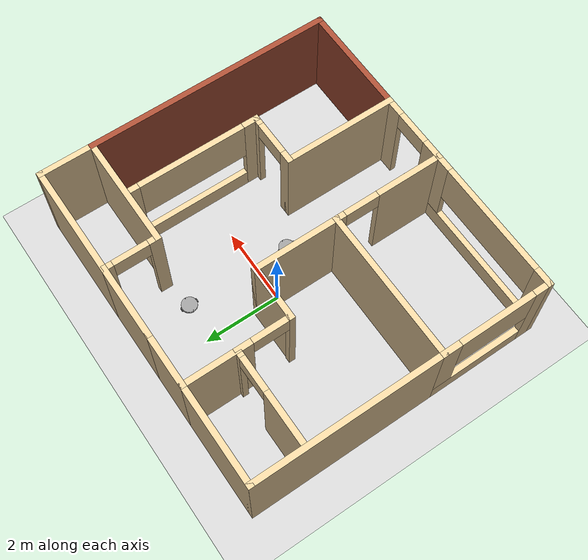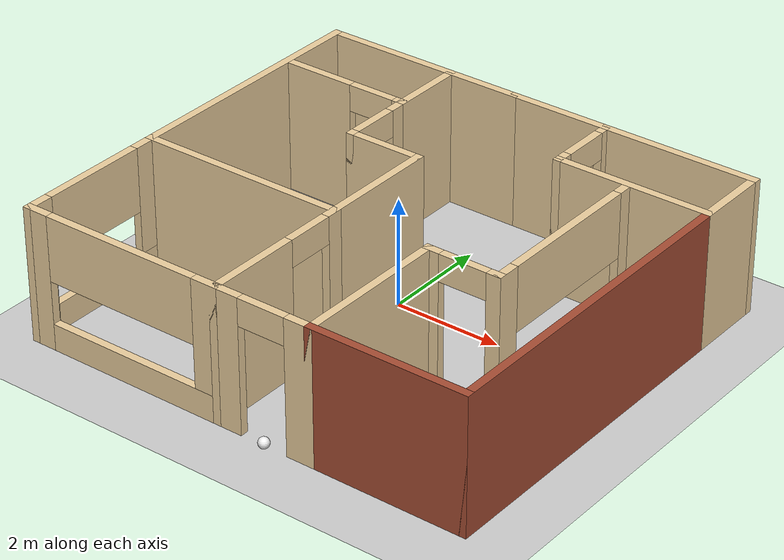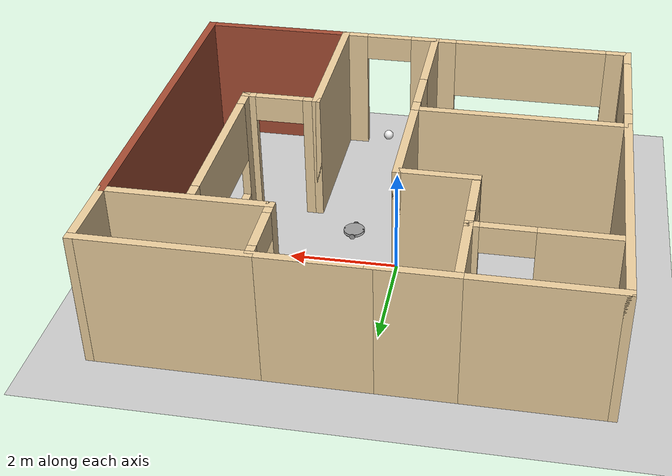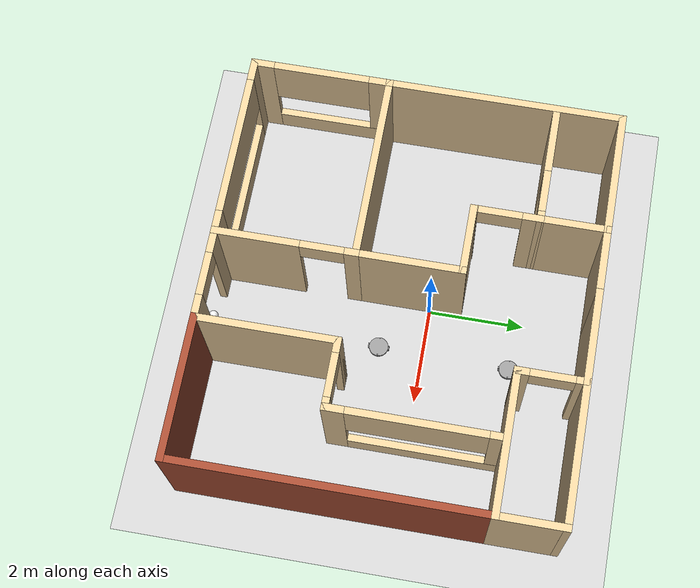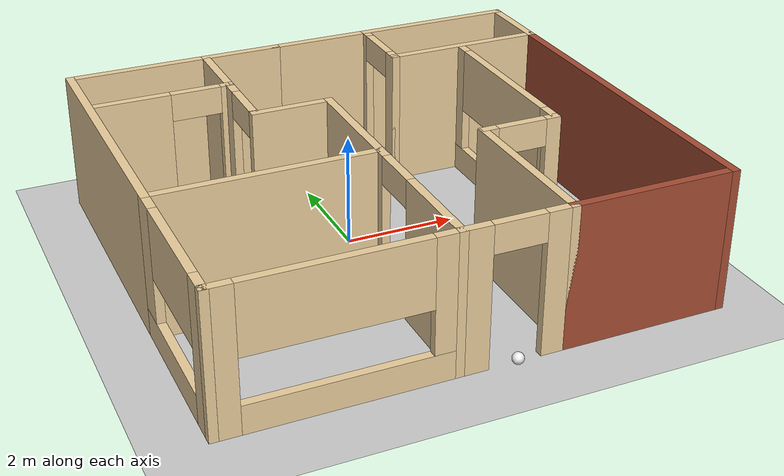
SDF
<sdf version="1.6">
 <world name="default">
  <plugin name="hello" filename="libhello.so"/>
  <light name="sun" type="directional">
   <pose>0 0 10 0 -0 0</pose>
   <diffuse>0.8 0.8 0.8 1</diffuse>
   <specular>0.2 0.2 0.2 1</specular>
   <attenuation>
    <range>1000</range>
    <constant>0.9</constant>
    <linear>0.01</linear>
    <quadratic>0.001</quadratic>
   </attenuation>
   <direction>-0.5 0.1 -0.9</direction>
  </light>
  <model name="ground_plane">
   <static>1</static>
   <link name="link">
    <collision name="collision">
     <geometry><plane><normal>0 0 1</normal><size>100 100</size></plane></geometry>
     <surface><friction><ode><mu>100</mu><mu2>50</mu2></ode></friction></surface>
    </collision>
    <visual name="visual">
     <cast_shadows>0</cast_shadows>
     <geometry><plane><normal>0 0 1</normal><size>100 100</size></plane></geometry>
     <material>
      <script><uri>file://media/materials/scripts/gazebo.material</uri><name>Gazebo/Grey</name></script>
     </material>
    </visual>
   </link>
  </model>
  <gravity>0 0 -9.8</gravity>
  <magnetic_field>6e-06 2.3e-05 -4.2e-05</magnetic_field>
  <atmosphere type="adiabatic"/>
  <physics name="default_physics" default="0" type="ode">
   <max_step_size>0.001</max_step_size>
   <real_time_factor>1</real_time_factor>
   <real_time_update_rate>1000</real_time_update_rate>
  </physics>
  <scene><ambient>0.4 0.4 0.4 1</ambient><background>0.7 0.7 0.7 1</background><shadows>1</shadows></scene>
  <spherical_coordinates>
   <surface_model>EARTH_WGS84</surface_model>
   <latitude_deg>0</latitude_deg>
   <longitude_deg>0</longitude_deg>
   <elevation>0</elevation>
   <heading_deg>0</heading_deg>
  </spherical_coordinates>
  <model name="MyHouse">
   <pose>0.33708 -0.54401 0 0 -0 0</pose>
   <link name="Wall_0">
    <pose>-2.35 -3.85 0 0 -0 0</pose>
    <visual name="Wall_0_Visual_0">
     <pose>-1.7526 0 1.25 0 -0 0</pose>
     <geometry><box><size>0.494799 0.15 2.5</size></box></geometry>
     <material>
      <script><uri>file://media/materials/scripts/gazebo.material</uri><name>Gazebo/Grey</name></script>
      <ambient>0.921569 0.807843 0.615686 1</ambient>
     </material>
     <meta><layer>0</layer></meta>
    </visual>
    <collision name="Wall_0_Collision_0">
     <geometry><box><size>0.494799 0.15 2.5</size></box></geometry>
     <pose>-1.7526 0 1.25 0 -0 0</pose>
    </collision>
    <visual name="Wall_0_Visual_1">
     <pose>0.2474 0 0.25 0 -0 0</pose>
     <geometry><box><size>3.5052 0.15 0.5</size></box></geometry>
     <material>
      <script><uri>file://media/materials/scripts/gazebo.material</uri><name>Gazebo/Grey</name></script>
      <ambient>0.921569 0.807843 0.615686 1</ambient>
     </material>
     <meta><layer>0</layer></meta>
    </visual>
    <collision name="Wall_0_Collision_1">
     <geometry><box><size>3.5052 0.15 0.5</size></box></geometry>
     <pose>0.2474 0 0.25 0 -0 0</pose>
    </collision>
    <visual name="Wall_0_Visual_2">
     <pose>1.7474 0 1.5 0 -0 0</pose>
     <geometry><box><size>0.505201 0.15 2</size></box></geometry>
     <material>
      <script><uri>file://media/materials/scripts/gazebo.material</uri><name>Gazebo/Grey</name></script>
      <ambient>0.921569 0.807843 0.615686 1</ambient>
     </material>
     <meta><layer>0</layer></meta>
    </visual>
    <collision name="Wall_0_Collision_2">
     <geometry><box><size>0.505201 0.15 2</size></box></geometry>
     <pose>1.7474 0 1.5 0 -0 0</pose>
    </collision>
    <visual name="Wall_0_Visual_3">
     <pose>-0.005201 0 1.9 0 -0 0</pose>
     <geometry><box><size>3 0.15 1.2</size></box></geometry>
     <material>
      <script><uri>file://media/materials/scripts/gazebo.material</uri><name>Gazebo/Grey</name></script>
      <ambient>0.921569 0.807843 0.615686 1</ambient>
     </material>
     <meta><layer>0</layer></meta>
    </visual>
    <collision name="Wall_0_Collision_3">
     <geometry><box><size>3 0.15 1.2</size></box></geometry>
     <pose>-0.005201 0 1.9 0 -0 0</pose>
    </collision>
   </link>
   <link name="Wall_12">
    <pose>-4.275 -2.425 0 0 -0 1.5708</pose>
    <visual name="Wall_12_Visual_0">
     <pose>-1.25263 0 1.25 0 -0 0</pose>
     <geometry><box><size>0.494741 0.15 2.5</size></box></geometry>
     <material>
      <script><uri>file://media/materials/scripts/gazebo.material</uri><name>Gazebo/Grey</name></script>
      <ambient>0.921569 0.807843 0.615686 1</ambient>
     </material>
     <meta><layer>0</layer></meta>
    </visual>
    <collision name="Wall_12_Collision_0">
     <geometry><box><size>0.494741 0.15 2.5</size></box></geometry>
     <pose>-1.25263 0 1.25 0 -0 0</pose>
    </collision>
    <visual name="Wall_12_Visual_1">
     <pose>0.247371 0 0.25 0 -0 0</pose>
     <geometry><box><size>2.50526 0.15 0.5</size></box></geometry>
     <material>
      <script><uri>file://media/materials/scripts/gazebo.material</uri><name>Gazebo/Grey</name></script>
      <ambient>0.921569 0.807843 0.615686 1</ambient>
     </material>
     <meta><layer>0</layer></meta>
    </visual>
    <collision name="Wall_12_Collision_1">
     <geometry><box><size>2.50526 0.15 0.5</size></box></geometry>
     <pose>0.247371 0 0.25 0 -0 0</pose>
    </collision>
    <visual name="Wall_12_Visual_2">
     <pose>1.24737 0 1.5 0 -0 0</pose>
     <geometry><box><size>0.505259 0.15 2</size></box></geometry>
     <material>
      <script><uri>file://media/materials/scripts/gazebo.material</uri><name>Gazebo/Grey</name></script>
      <ambient>0.921569 0.807843 0.615686 1</ambient>
     </material>
     <meta><layer>0</layer></meta>
    </visual>
    <collision name="Wall_12_Collision_2">
     <geometry><box><size>0.505259 0.15 2</size></box></geometry>
     <pose>1.24737 0 1.5 0 -0 0</pose>
    </collision>
    <visual name="Wall_12_Visual_3">
     <pose>-0.005259 0 1.9 0 -0 0</pose>
     <geometry><box><size>2 0.15 1.2</size></box></geometry>
     <material>
      <script><uri>file://media/materials/scripts/gazebo.material</uri><name>Gazebo/Grey</name></script>
      <ambient>0.921569 0.807843 0.615686 1</ambient>
     </material>
     <meta><layer>0</layer></meta>
    </visual>
    <collision name="Wall_12_Collision_3">
     <geometry><box><size>2 0.15 1.2</size></box></geometry>
     <pose>-0.005259 0 1.9 0 -0 0</pose>
    </collision>
   </link>
   <link name="Wall_18">
    <collision name="Wall_18_Collision">
     <geometry><box><size>4 0.15 2.5</size></box></geometry>
     <pose>0 0 1.25 0 -0 0</pose>
    </collision>
    <visual name="Wall_18_Visual">
     <pose>0 0 1.25 0 -0 0</pose>
     <geometry><box><size>4 0.15 2.5</size></box></geometry>
     <material>
      <script><uri>file://media/materials/scripts/gazebo.material</uri><name>Gazebo/Grey</name></script>
      <ambient>0.921569 0.807843 0.615686 1</ambient>
     </material>
     <meta><layer>0</layer></meta>
    </visual>
    <pose>-2.35 -1 0 0 -0 0</pose>
   </link>
   <link name="Wall_19">
    <pose>-0.425 -2.425 0 0 0 -1.5708</pose>
    <visual name="Wall_19_Visual_0">
     <pose>-1.34808 0 1.25 0 -0 0</pose>
     <geometry><box><size>0.303841 0.15 2.5</size></box></geometry>
     <material>
      <script><uri>file://media/materials/scripts/gazebo.material</uri><name>Gazebo/Grey</name></script>
      <ambient>0.921569 0.807843 0.615686 1</ambient>
     </material>
     <meta><layer>0</layer></meta>
    </visual>
    <collision name="Wall_19_Collision_0">
     <geometry><box><size>0.303841 0.15 2.5</size></box></geometry>
     <pose>-1.34808 0 1.25 0 -0 0</pose>
    </collision>
    <visual name="Wall_19_Visual_1">
     <pose>0.601921 0 1.25 0 -0 0</pose>
     <geometry><box><size>1.79616 0.15 2.5</size></box></geometry>
     <material>
      <script><uri>file://media/materials/scripts/gazebo.material</uri><name>Gazebo/Grey</name></script>
      <ambient>0.921569 0.807843 0.615686 1</ambient>
     </material>
     <meta><layer>0</layer></meta>
    </visual>
    <collision name="Wall_19_Collision_1">
     <geometry><box><size>1.79616 0.15 2.5</size></box></geometry>
     <pose>0.601921 0 1.25 0 -0 0</pose>
    </collision>
    <visual name="Wall_19_Visual_2">
     <pose>-0.746159 0 2.25 0 -0 0</pose>
     <geometry><box><size>0.9 0.15 0.5</size></box></geometry>
     <material>
      <script><uri>file://media/materials/scripts/gazebo.material</uri><name>Gazebo/Grey</name></script>
      <ambient>0.921569 0.807843 0.615686 1</ambient>
     </material>
     <meta><layer>0</layer></meta>
    </visual>
    <collision name="Wall_19_Collision_2">
     <geometry><box><size>0.9 0.15 0.5</size></box></geometry>
     <pose>-0.746159 0 2.25 0 -0 0</pose>
    </collision>
   </link>
   <link name="Wall_21">
    <pose>0.5 -3.85 0 0 -0 0</pose>
    <visual name="Wall_21_Visual_0">
     <pose>-0.718803 0 1.25 0 -0 0</pose>
     <geometry><box><size>0.562395 0.15 2.5</size></box></geometry>
     <material>
      <script><uri>file://media/materials/scripts/gazebo.material</uri><name>Gazebo/Grey</name></script>
      <ambient>0.921569 0.807843 0.615686 1</ambient>
     </material>
     <meta><layer>0</layer></meta>
    </visual>
    <collision name="Wall_21_Collision_0">
     <geometry><box><size>0.562395 0.15 2.5</size></box></geometry>
     <pose>-0.718803 0 1.25 0 -0 0</pose>
    </collision>
    <visual name="Wall_21_Visual_1">
     <pose>0.731197 0 1.25 0 -0 0</pose>
     <geometry><box><size>0.537605 0.15 2.5</size></box></geometry>
     <material>
      <script><uri>file://media/materials/scripts/gazebo.material</uri><name>Gazebo/Grey</name></script>
      <ambient>0.921569 0.807843 0.615686 1</ambient>
     </material>
     <meta><layer>0</layer></meta>
    </visual>
    <collision name="Wall_21_Collision_1">
     <geometry><box><size>0.537605 0.15 2.5</size></box></geometry>
     <pose>0.731197 0 1.25 0 -0 0</pose>
    </collision>
    <visual name="Wall_21_Visual_2">
     <pose>0.012395 0 2.25 0 -0 0</pose>
     <geometry><box><size>0.9 0.15 0.5</size></box></geometry>
     <material>
      <script><uri>file://media/materials/scripts/gazebo.material</uri><name>Gazebo/Grey</name></script>
      <ambient>0.921569 0.807843 0.615686 1</ambient>
     </material>
     <meta><layer>0</layer></meta>
    </visual>
    <collision name="Wall_21_Collision_2">
     <geometry><box><size>0.9 0.15 0.5</size></box></geometry>
     <pose>0.012395 0 2.25 0 -0 0</pose>
    </collision>
   </link>
   <link name="Wall_22">
    <collision name="Wall_22_Collision">
     <geometry><box><size>3 0.15 2.5</size></box></geometry>
     <pose>0 0 1.25 0 -0 0</pose>
    </collision>
    <visual name="Wall_22_Visual">
     <pose>0 0 1.25 0 -0 0</pose>
     <geometry><box><size>3 0.15 2.5</size></box></geometry>
     <material>
      <script><uri>file://media/materials/scripts/gazebo.material</uri><name>Gazebo/Grey</name></script>
      <ambient>0.921569 0.807843 0.615686 1</ambient>
     </material>
     <meta><layer>0</layer></meta>
    </visual>
    <pose>1.425 -2.425 0 0 -0 1.5708</pose>
   </link>
   <link name="Wall_23">
    <pose>2.1 -1 0 0 -0 0</pose>
    <visual name="Wall_23_Visual_0">
     <pose>-0.586497 0 1.25 0 -0 0</pose>
     <geometry><box><size>0.327005 0.15 2.5</size></box></geometry>
     <material>
      <script><uri>file://media/materials/scripts/gazebo.material</uri><name>Gazebo/Grey</name></script>
      <ambient>0.921569 0.807843 0.615686 1</ambient>
     </material>
     <meta><layer>0</layer></meta>
    </visual>
    <collision name="Wall_23_Collision_0">
     <geometry><box><size>0.327005 0.15 2.5</size></box></geometry>
     <pose>-0.586497 0 1.25 0 -0 0</pose>
    </collision>
    <visual name="Wall_23_Visual_1">
     <pose>0.613503 0 1.25 0 -0 0</pose>
     <geometry><box><size>0.272995 0.15 2.5</size></box></geometry>
     <material>
      <script><uri>file://media/materials/scripts/gazebo.material</uri><name>Gazebo/Grey</name></script>
      <ambient>0.921569 0.807843 0.615686 1</ambient>
     </material>
     <meta><layer>0</layer></meta>
    </visual>
    <collision name="Wall_23_Collision_1">
     <geometry><box><size>0.272995 0.15 2.5</size></box></geometry>
     <pose>0.613503 0 1.25 0 -0 0</pose>
    </collision>
    <visual name="Wall_23_Visual_2">
     <pose>0.027005 0 2.25 0 -0 0</pose>
     <geometry><box><size>0.9 0.15 0.5</size></box></geometry>
     <material>
      <script><uri>file://media/materials/scripts/gazebo.material</uri><name>Gazebo/Grey</name></script>
      <ambient>0.921569 0.807843 0.615686 1</ambient>
     </material>
     <meta><layer>0</layer></meta>
    </visual>
    <collision name="Wall_23_Collision_2">
     <geometry><box><size>0.9 0.15 0.5</size></box></geometry>
     <pose>0.027005 0 2.25 0 -0 0</pose>
    </collision>
   </link>
   <link name="Wall_25">
    <collision name="Wall_25_Collision">
     <geometry><box><size>3 0.15 2.5</size></box></geometry>
     <pose>0 0 1.25 0 -0 0</pose>
    </collision>
    <visual name="Wall_25_Visual">
     <pose>0 0 1.25 0 -0 0</pose>
     <geometry><box><size>3 0.15 2.5</size></box></geometry>
     <material>
      <script><uri>file://media/materials/scripts/gazebo.material</uri><name>Gazebo/Bricks</name></script>
      <ambient>1 1 1 1</ambient>
     </material>
     <meta><layer>0</layer></meta>
    </visual>
    <pose>2.85 -3.85 0 0 -0 0</pose>
   </link>
   <link name="Wall_28">
    <collision name="Wall_28_Collision">
     <geometry><box><size>6.5 0.15 2.5</size></box></geometry>
     <pose>0 0 1.25 0 -0 0</pose>
    </collision>
    <visual name="Wall_28_Visual">
     <pose>0 0 1.25 0 -0 0</pose>
     <geometry><box><size>6.5 0.15 2.5</size></box></geometry>
     <material>
      <script><uri>file://media/materials/scripts/gazebo.material</uri><name>Gazebo/Bricks</name></script>
      <ambient>1 1 1 1</ambient>
     </material>
     <meta><layer>0</layer></meta>
    </visual>
    <pose>4.275 -0.675 0 0 -0 1.5708</pose>
   </link>
   <link name="Wall_31">
    <collision name="Wall_31_Collision">
     <geometry><box><size>1.5 0.15 2.5</size></box></geometry>
     <pose>0 0 1.25 0 -0 0</pose>
    </collision>
    <visual name="Wall_31_Visual">
     <pose>0 0 1.25 0 -0 0</pose>
     <geometry><box><size>1.5 0.15 2.5</size></box></geometry>
     <material>
      <script><uri>file://media/materials/scripts/gazebo.material</uri><name>Gazebo/Grey</name></script>
      <ambient>0.921569 0.807843 0.615686 1</ambient>
     </material>
     <meta><layer>0</layer></meta>
    </visual>
    <pose>4.275 3.175 0 0 -0 1.5708</pose>
   </link>
   <link name="Wall_32">
    <collision name="Wall_32_Collision">
     <geometry><box><size>3 0.15 2.5</size></box></geometry>
     <pose>0 0 1.25 0 -0 0</pose>
    </collision>
    <visual name="Wall_32_Visual">
     <pose>0 0 1.25 0 -0 0</pose>
     <geometry><box><size>3 0.15 2.5</size></box></geometry>
     <material>
      <script><uri>file://media/materials/scripts/gazebo.material</uri><name>Gazebo/Grey</name></script>
      <ambient>0.921569 0.807843 0.615686 1</ambient>
     </material>
     <meta><layer>0</layer></meta>
    </visual>
    <pose>2.85 3.85 0 0 -0 3.14159</pose>
   </link>
   <link name="Wall_33">
    <pose>1.425 3.175 0 0 0 -1.5708</pose>
    <visual name="Wall_33_Visual_0">
     <pose>-0.605329 0 1.25 0 -0 0</pose>
     <geometry><box><size>0.289342 0.15 2.5</size></box></geometry>
     <material>
      <script><uri>file://media/materials/scripts/gazebo.material</uri><name>Gazebo/Grey</name></script>
      <ambient>0.921569 0.807843 0.615686 1</ambient>
     </material>
     <meta><layer>0</layer></meta>
    </visual>
    <collision name="Wall_33_Collision_0">
     <geometry><box><size>0.289342 0.15 2.5</size></box></geometry>
     <pose>-0.605329 0 1.25 0 -0 0</pose>
    </collision>
    <visual name="Wall_33_Visual_1">
     <pose>0.594671 0 1.25 0 -0 0</pose>
     <geometry><box><size>0.310658 0.15 2.5</size></box></geometry>
     <material>
      <script><uri>file://media/materials/scripts/gazebo.material</uri><name>Gazebo/Grey</name></script>
      <ambient>0.921569 0.807843 0.615686 1</ambient>
     </material>
     <meta><layer>0</layer></meta>
    </visual>
    <collision name="Wall_33_Collision_1">
     <geometry><box><size>0.310658 0.15 2.5</size></box></geometry>
     <pose>0.594671 0 1.25 0 -0 0</pose>
    </collision>
    <visual name="Wall_33_Visual_2">
     <pose>-0.010658 0 2.25 0 -0 0</pose>
     <geometry><box><size>0.9 0.15 0.5</size></box></geometry>
     <material>
      <script><uri>file://media/materials/scripts/gazebo.material</uri><name>Gazebo/Grey</name></script>
      <ambient>0.921569 0.807843 0.615686 1</ambient>
     </material>
     <meta><layer>0</layer></meta>
    </visual>
    <collision name="Wall_33_Collision_2">
     <geometry><box><size>0.9 0.15 0.5</size></box></geometry>
     <pose>-0.010658 0 2.25 0 -0 0</pose>
    </collision>
   </link>
   <link name="Wall_34">
    <collision name="Wall_34_Collision">
     <geometry><box><size>3 0.15 2.5</size></box></geometry>
     <pose>0 0 1.25 0 -0 0</pose>
    </collision>
    <visual name="Wall_34_Visual">
     <pose>0 0 1.25 0 -0 0</pose>
     <geometry><box><size>3 0.15 2.5</size></box></geometry>
     <material>
      <script><uri>file://media/materials/scripts/gazebo.material</uri><name>Gazebo/Grey</name></script>
      <ambient>0.921569 0.807843 0.615686 1</ambient>
     </material>
     <meta><layer>0</layer></meta>
    </visual>
    <pose>2.85 2.5 0 0 -0 0</pose>
   </link>
   <link name="Wall_36">
    <pose>2.775 0.675 0 0 -0 1.5708</pose>
    <visual name="Wall_36_Visual_0">
     <pose>-1.52494 0 1.25 0 -0 0</pose>
     <geometry><box><size>0.450112 0.15 2.5</size></box></geometry>
     <material>
      <script><uri>file://media/materials/scripts/gazebo.material</uri><name>Gazebo/Grey</name></script>
      <ambient>0.921569 0.807843 0.615686 1</ambient>
     </material>
     <meta><layer>0</layer></meta>
    </visual>
    <collision name="Wall_36_Collision_0">
     <geometry><box><size>0.450112 0.15 2.5</size></box></geometry>
     <pose>-1.52494 0 1.25 0 -0 0</pose>
    </collision>
    <visual name="Wall_36_Visual_1">
     <pose>0.225056 0 0.25 0 -0 0</pose>
     <geometry><box><size>3.04989 0.15 0.5</size></box></geometry>
     <material>
      <script><uri>file://media/materials/scripts/gazebo.material</uri><name>Gazebo/Grey</name></script>
      <ambient>0.921569 0.807843 0.615686 1</ambient>
     </material>
     <meta><layer>0</layer></meta>
    </visual>
    <collision name="Wall_36_Collision_1">
     <geometry><box><size>3.04989 0.15 0.5</size></box></geometry>
     <pose>0.225056 0 0.25 0 -0 0</pose>
    </collision>
    <visual name="Wall_36_Visual_2">
     <pose>1.62506 0 1.5 0 -0 0</pose>
     <geometry><box><size>0.249888 0.15 2</size></box></geometry>
     <material>
      <script><uri>file://media/materials/scripts/gazebo.material</uri><name>Gazebo/Grey</name></script>
      <ambient>0.921569 0.807843 0.615686 1</ambient>
     </material>
     <meta><layer>0</layer></meta>
    </visual>
    <collision name="Wall_36_Collision_2">
     <geometry><box><size>0.249888 0.15 2</size></box></geometry>
     <pose>1.62506 0 1.5 0 -0 0</pose>
    </collision>
    <visual name="Wall_36_Visual_3">
     <pose>0.100112 0 1.9 0 -0 0</pose>
     <geometry><box><size>2.8 0.15 1.2</size></box></geometry>
     <material>
      <script><uri>file://media/materials/scripts/gazebo.material</uri><name>Gazebo/Grey</name></script>
      <ambient>0.921569 0.807843 0.615686 1</ambient>
     </material>
     <meta><layer>0</layer></meta>
    </visual>
    <collision name="Wall_36_Collision_3">
     <geometry><box><size>2.8 0.15 1.2</size></box></geometry>
     <pose>0.100112 0 1.9 0 -0 0</pose>
    </collision>
   </link>
   <link name="Wall_38">
    <collision name="Wall_38_Collision">
     <geometry><box><size>2 0.15 2.5</size></box></geometry>
     <pose>0 0 1.25 0 -0 0</pose>
    </collision>
    <visual name="Wall_38_Visual">
     <pose>0 0 1.25 0 -0 0</pose>
     <geometry><box><size>2 0.15 2.5</size></box></geometry>
     <material>
      <script><uri>file://media/materials/scripts/gazebo.material</uri><name>Gazebo/Grey</name></script>
      <ambient>0.921569 0.807843 0.615686 1</ambient>
     </material>
     <meta><layer>0</layer></meta>
    </visual>
    <pose>0.5 3.85 0 0 -0 3.14159</pose>
   </link>
   <link name="Wall_39">
    <collision name="Wall_39_Collision">
     <geometry><box><size>1.5 0.15 2.5</size></box></geometry>
     <pose>0 0 1.25 0 -0 0</pose>
    </collision>
    <visual name="Wall_39_Visual">
     <pose>0 0 1.25 0 -0 0</pose>
     <geometry><box><size>1.5 0.15 2.5</size></box></geometry>
     <material>
      <script><uri>file://media/materials/scripts/gazebo.material</uri><name>Gazebo/Grey</name></script>
      <ambient>0.921569 0.807843 0.615686 1</ambient>
     </material>
     <meta><layer>0</layer></meta>
    </visual>
    <pose>-1.1 3.85 0 0 -0 3.14159</pose>
   </link>
   <link name="Wall_43">
    <collision name="Wall_43_Collision">
     <geometry><box><size>1.5 0.15 2.5</size></box></geometry>
     <pose>0 0 1.25 0 -0 0</pose>
    </collision>
    <visual name="Wall_43_Visual">
     <pose>0 0 1.25 0 -0 0</pose>
     <geometry><box><size>1.5 0.15 2.5</size></box></geometry>
     <material>
      <script><uri>file://media/materials/scripts/gazebo.material</uri><name>Gazebo/Grey</name></script>
      <ambient>0.921569 0.807843 0.615686 1</ambient>
     </material>
     <meta><layer>0</layer></meta>
    </visual>
    <pose>-1.775 3.175 0 0 -0 1.5708</pose>
   </link>
   <link name="Wall_48">
    <collision name="Wall_48_Collision">
     <geometry><box><size>5 0.15 2.5</size></box></geometry>
     <pose>0 0 1.25 0 -0 0</pose>
    </collision>
    <visual name="Wall_48_Visual">
     <pose>0 0 1.25 0 -0 0</pose>
     <geometry><box><size>5 0.15 2.5</size></box></geometry>
     <material>
      <script><uri>file://media/materials/scripts/gazebo.material</uri><name>Gazebo/Grey</name></script>
      <ambient>0.921569 0.807843 0.615686 1</ambient>
     </material>
     <meta><layer>0</layer></meta>
    </visual>
    <pose>-4.275 1.425 0 0 -0 1.5708</pose>
   </link>
   <link name="Wall_49">
    <collision name="Wall_49_Collision">
     <geometry><box><size>2.65 0.15 2.5</size></box></geometry>
     <pose>0 0 1.25 0 -0 0</pose>
    </collision>
    <visual name="Wall_49_Visual">
     <pose>0 0 1.25 0 -0 0</pose>
     <geometry><box><size>2.65 0.15 2.5</size></box></geometry>
     <material>
      <script><uri>file://media/materials/scripts/gazebo.material</uri><name>Gazebo/Grey</name></script>
      <ambient>0.921569 0.807843 0.615686 1</ambient>
     </material>
     <meta><layer>0</layer></meta>
    </visual>
    <pose>-3.025 3.85 0 0 -0 0</pose>
   </link>
   <link name="Wall_51">
    <pose>-2.95 2.5 0 0 -0 3.14159</pose>
    <visual name="Wall_51_Visual_0">
     <pose>-1.12577 0 1.25 0 -0 0</pose>
     <geometry><box><size>0.248452 0.15 2.5</size></box></geometry>
     <material>
      <script><uri>file://media/materials/scripts/gazebo.material</uri><name>Gazebo/Grey</name></script>
      <ambient>0.921569 0.807843 0.615686 1</ambient>
     </material>
     <meta><layer>0</layer></meta>
    </visual>
    <collision name="Wall_51_Collision_0">
     <geometry><box><size>0.248452 0.15 2.5</size></box></geometry>
     <pose>-1.12577 0 1.25 0 -0 0</pose>
    </collision>
    <visual name="Wall_51_Visual_1">
     <pose>0.574226 0 1.25 0 -0 0</pose>
     <geometry><box><size>1.35155 0.15 2.5</size></box></geometry>
     <material>
      <script><uri>file://media/materials/scripts/gazebo.material</uri><name>Gazebo/Grey</name></script>
      <ambient>0.921569 0.807843 0.615686 1</ambient>
     </material>
     <meta><layer>0</layer></meta>
    </visual>
    <collision name="Wall_51_Collision_1">
     <geometry><box><size>1.35155 0.15 2.5</size></box></geometry>
     <pose>0.574226 0 1.25 0 -0 0</pose>
    </collision>
    <visual name="Wall_51_Visual_2">
     <pose>-0.551548 0 2.25 0 -0 0</pose>
     <geometry><box><size>0.9 0.15 0.5</size></box></geometry>
     <material>
      <script><uri>file://media/materials/scripts/gazebo.material</uri><name>Gazebo/Grey</name></script>
      <ambient>0.921569 0.807843 0.615686 1</ambient>
     </material>
     <meta><layer>0</layer></meta>
    </visual>
    <collision name="Wall_51_Collision_2">
     <geometry><box><size>0.9 0.15 0.5</size></box></geometry>
     <pose>-0.551548 0 2.25 0 -0 0</pose>
    </collision>
   </link>
   <link name="Wall_53">
    <pose>-1.775 1.825 0 0 0 -1.5708</pose>
    <visual name="Wall_53_Visual_0">
     <pose>-0.532233 0 1.25 0 -0 0</pose>
     <geometry><box><size>0.435535 0.15 2.5</size></box></geometry>
     <material>
      <script><uri>file://media/materials/scripts/gazebo.material</uri><name>Gazebo/Grey</name></script>
      <ambient>0.921569 0.807843 0.615686 1</ambient>
     </material>
     <meta><layer>0</layer></meta>
    </visual>
    <collision name="Wall_53_Collision_0">
     <geometry><box><size>0.435535 0.15 2.5</size></box></geometry>
     <pose>-0.532233 0 1.25 0 -0 0</pose>
    </collision>
    <visual name="Wall_53_Visual_1">
     <pose>0.667767 0 1.25 0 -0 0</pose>
     <geometry><box><size>0.164465 0.15 2.5</size></box></geometry>
     <material>
      <script><uri>file://media/materials/scripts/gazebo.material</uri><name>Gazebo/Grey</name></script>
      <ambient>0.921569 0.807843 0.615686 1</ambient>
     </material>
     <meta><layer>0</layer></meta>
    </visual>
    <collision name="Wall_53_Collision_1">
     <geometry><box><size>0.164465 0.15 2.5</size></box></geometry>
     <pose>0.667767 0 1.25 0 -0 0</pose>
    </collision>
    <visual name="Wall_53_Visual_2">
     <pose>0.135535 0 2.25 0 -0 0</pose>
     <geometry><box><size>0.9 0.15 0.5</size></box></geometry>
     <material>
      <script><uri>file://media/materials/scripts/gazebo.material</uri><name>Gazebo/Grey</name></script>
      <ambient>0.921569 0.807843 0.615686 1</ambient>
     </material>
     <meta><layer>0</layer></meta>
    </visual>
    <collision name="Wall_53_Collision_2">
     <geometry><box><size>0.9 0.15 0.5</size></box></geometry>
     <pose>0.135535 0 2.25 0 -0 0</pose>
    </collision>
   </link>
   <link name="Wall_54">
    <collision name="Wall_54_Collision">
     <geometry><box><size>1.5 0.15 2.5</size></box></geometry>
     <pose>0 0 1.25 0 -0 0</pose>
    </collision>
    <visual name="Wall_54_Visual">
     <pose>0 0 1.25 0 -0 0</pose>
     <geometry><box><size>1.5 0.15 2.5</size></box></geometry>
     <material>
      <script><uri>file://media/materials/scripts/gazebo.material</uri><name>Gazebo/Grey</name></script>
      <ambient>0.921569 0.807843 0.615686 1</ambient>
     </material>
     <meta><layer>0</layer></meta>
    </visual>
    <pose>-1.1 1.15 0 0 -0 0</pose>
   </link>
   <link name="Wall_55">
    <collision name="Wall_55_Collision">
     <geometry><box><size>2.3 0.15 2.5</size></box></geometry>
     <pose>0 0 1.25 0 -0 0</pose>
    </collision>
    <visual name="Wall_55_Visual">
     <pose>0 0 1.25 0 -0 0</pose>
     <geometry><box><size>2.3 0.15 2.5</size></box></geometry>
     <material>
      <script><uri>file://media/materials/scripts/gazebo.material</uri><name>Gazebo/Grey</name></script>
      <ambient>0.921569 0.807843 0.615686 1</ambient>
     </material>
     <meta><layer>0</layer></meta>
    </visual>
    <pose>-0.425 0.075 0 0 0 -1.5708</pose>
   </link>
   <static>1</static>
  </model>
  <model name="MyRobot">
   <link name="link_0">
    <pose>0 0 -0.02125 0 -0 0</pose>
    <inertial>
     <mass>1</mass>
     <inertia><ixx>0.145833</ixx><ixy>0</ixy><ixz>0</ixz><iyy>0.145833</iyy><iyz>0</iyz><izz>0.125</izz></inertia>
    </inertial>
    <visual name="visual">
     <geometry><cylinder><radius>0.2</radius><length>0.01</length></cylinder></geometry>
     <material>
      <lighting>1</lighting>
      <script><uri>file://media/materials/scripts/gazebo.material</uri><name>Gazebo/Grey</name></script>
      <ambient>0.3 0.3 0.3 1</ambient>
      <diffuse>0.7 0.7 0.7 1</diffuse>
      <specular>0.01 0.01 0.01 1</specular>
      <emissive>0 0 0 1</emissive>
      <shader type="vertex"><normal_map>__default__</normal_map></shader>
     </material>
    </visual>
    <collision name="collision">
     <geometry><cylinder><radius>0.2</radius><length>0.01</length></cylinder></geometry>
     <surface>
      <friction>
       <ode><mu>1</mu><mu2>1</mu2><fdir1>0 0 0</fdir1><slip1>0</slip1><slip2>0</slip2></ode>
       <torsional>
        <coefficient>1</coefficient>
        <patch_radius>0</patch_radius>
        <surface_radius>0</surface_radius>
        <use_patch_radius>1</use_patch_radius>
        <ode><slip>0</slip></ode>
       </torsional>
      </friction>
      <bounce><restitution_coefficient>0</restitution_coefficient><threshold>1e+06</threshold></bounce>
      <contact>
       <collide_without_contact>0</collide_without_contact>
       <collide_without_contact_bitmask>1</collide_without_contact_bitmask>
       <collide_bitmask>1</collide_bitmask>
       <ode>
        <soft_cfm>0</soft_cfm>
        <soft_erp>0.2</soft_erp>
        <kp>1e+13</kp>
        <kd>1</kd>
        <max_vel>0.01</max_vel>
        <min_depth>0</min_depth>
       </ode>
       <bullet>
        <split_impulse>1</split_impulse>
        <split_impulse_penetration_threshold>-0.01</split_impulse_penetration_threshold>
        <soft_cfm>0</soft_cfm>
        <soft_erp>0.2</soft_erp>
        <kp>1e+13</kp>
        <kd>1</kd>
       </bullet>
      </contact>
     </surface>
    </collision>
   </link>
   <link name="link_0_clone">
    <pose>0 0 0.02875 0 -0 0</pose>
    <inertial>
     <mass>1</mass>
     <inertia><ixx>0.145833</ixx><ixy>0</ixy><ixz>0</ixz><iyy>0.145833</iyy><iyz>0</iyz><izz>0.125</izz></inertia>
    </inertial>
    <visual name="visual">
     <geometry><cylinder><radius>0.2</radius><length>0.01</length></cylinder></geometry>
     <material>
      <lighting>1</lighting>
      <script><uri>file://media/materials/scripts/gazebo.material</uri><name>Gazebo/Grey</name></script>
      <ambient>0.3 0.3 0.3 1</ambient>
      <diffuse>0.7 0.7 0.7 1</diffuse>
      <specular>0.01 0.01 0.01 1</specular>
      <emissive>0 0 0 1</emissive>
      <shader type="vertex"><normal_map>__default__</normal_map></shader>
     </material>
    </visual>
    <collision name="collision">
     <geometry><cylinder><radius>0.2</radius><length>0.01</length></cylinder></geometry>
     <surface>
      <friction>
       <ode><mu>1</mu><mu2>1</mu2><fdir1>0 0 0</fdir1><slip1>0</slip1><slip2>0</slip2></ode>
       <torsional>
        <coefficient>1</coefficient>
        <patch_radius>0</patch_radius>
        <surface_radius>0</surface_radius>
        <use_patch_radius>1</use_patch_radius>
        <ode><slip>0</slip></ode>
       </torsional>
      </friction>
      <bounce><restitution_coefficient>0</restitution_coefficient><threshold>1e+06</threshold></bounce>
      <contact>
       <collide_without_contact>0</collide_without_contact>
       <collide_without_contact_bitmask>1</collide_without_contact_bitmask>
       <collide_bitmask>1</collide_bitmask>
       <ode>
        <soft_cfm>0</soft_cfm>
        <soft_erp>0.2</soft_erp>
        <kp>1e+13</kp>
        <kd>1</kd>
        <max_vel>0.01</max_vel>
        <min_depth>0</min_depth>
       </ode>
       <bullet>
        <split_impulse>1</split_impulse>
        <split_impulse_penetration_threshold>-0.01</split_impulse_penetration_threshold>
        <soft_cfm>0</soft_cfm>
        <soft_erp>0.2</soft_erp>
        <kp>1e+13</kp>
        <kd>1</kd>
       </bullet>
      </contact>
     </surface>
    </collision>
   </link>
   <link name="link_1">
    <pose>0.18 0 -0.00125 0 -0 0</pose>
    <inertial>
     <mass>1</mass>
     <inertia><ixx>0.145833</ixx><ixy>0</ixy><ixz>0</ixz><iyy>0.145833</iyy><iyz>0</iyz><izz>0.125</izz></inertia>
    </inertial>
    <visual name="visual">
     <geometry><cylinder><radius>0.01</radius><length>0.1</length></cylinder></geometry>
     <material>
      <lighting>1</lighting>
      <script><uri>file://media/materials/scripts/gazebo.material</uri><name>Gazebo/Grey</name></script>
      <ambient>0.3 0.3 0.3 1</ambient>
      <diffuse>0.7 0.7 0.7 1</diffuse>
      <specular>0.01 0.01 0.01 1</specular>
      <emissive>0 0 0 1</emissive>
      <shader type="vertex"><normal_map>__default__</normal_map></shader>
     </material>
    </visual>
    <collision name="collision">
     <geometry><cylinder><radius>0.01</radius><length>0.1</length></cylinder></geometry>
     <surface>
      <friction>
       <ode><mu>1</mu><mu2>1</mu2><fdir1>0 0 0</fdir1><slip1>0</slip1><slip2>0</slip2></ode>
       <torsional>
        <coefficient>1</coefficient>
        <patch_radius>0</patch_radius>
        <surface_radius>0</surface_radius>
        <use_patch_radius>1</use_patch_radius>
        <ode><slip>0</slip></ode>
       </torsional>
      </friction>
      <bounce><restitution_coefficient>0</restitution_coefficient><threshold>1e+06</threshold></bounce>
      <contact>
       <collide_without_contact>0</collide_without_contact>
       <collide_without_contact_bitmask>1</collide_without_contact_bitmask>
       <collide_bitmask>1</collide_bitmask>
       <ode>
        <soft_cfm>0</soft_cfm>
        <soft_erp>0.2</soft_erp>
        <kp>1e+13</kp>
        <kd>1</kd>
        <max_vel>0.01</max_vel>
        <min_depth>0</min_depth>
       </ode>
       <bullet>
        <split_impulse>1</split_impulse>
        <split_impulse_penetration_threshold>-0.01</split_impulse_penetration_threshold>
        <soft_cfm>0</soft_cfm>
        <soft_erp>0.2</soft_erp>
        <kp>1e+13</kp>
        <kd>1</kd>
       </bullet>
      </contact>
     </surface>
    </collision>
   </link>
   <link name="link_1_clone">
    <pose>-0.18 0 -0.00125 0 -0 0</pose>
    <inertial>
     <mass>1</mass>
     <inertia><ixx>0.145833</ixx><ixy>0</ixy><ixz>0</ixz><iyy>0.145833</iyy><iyz>0</iyz><izz>0.125</izz></inertia>
    </inertial>
    <visual name="visual">
     <geometry><cylinder><radius>0.01</radius><length>0.1</length></cylinder></geometry>
     <material>
      <lighting>1</lighting>
      <script><uri>file://media/materials/scripts/gazebo.material</uri><name>Gazebo/Grey</name></script>
      <ambient>0.3 0.3 0.3 1</ambient>
      <diffuse>0.7 0.7 0.7 1</diffuse>
      <specular>0.01 0.01 0.01 1</specular>
      <emissive>0 0 0 1</emissive>
      <shader type="vertex"><normal_map>__default__</normal_map></shader>
     </material>
    </visual>
    <collision name="collision">
     <geometry><cylinder><radius>0.01</radius><length>0.1</length></cylinder></geometry>
     <surface>
      <friction>
       <ode><mu>1</mu><mu2>1</mu2><fdir1>0 0 0</fdir1><slip1>0</slip1><slip2>0</slip2></ode>
       <torsional>
        <coefficient>1</coefficient>
        <patch_radius>0</patch_radius>
        <surface_radius>0</surface_radius>
        <use_patch_radius>1</use_patch_radius>
        <ode><slip>0</slip></ode>
       </torsional>
      </friction>
      <bounce><restitution_coefficient>0</restitution_coefficient><threshold>1e+06</threshold></bounce>
      <contact>
       <collide_without_contact>0</collide_without_contact>
       <collide_without_contact_bitmask>1</collide_without_contact_bitmask>
       <collide_bitmask>1</collide_bitmask>
       <ode>
        <soft_cfm>0</soft_cfm>
        <soft_erp>0.2</soft_erp>
        <kp>1e+13</kp>
        <kd>1</kd>
        <max_vel>0.01</max_vel>
        <min_depth>0</min_depth>
       </ode>
       <bullet>
        <split_impulse>1</split_impulse>
        <split_impulse_penetration_threshold>-0.01</split_impulse_penetration_threshold>
        <soft_cfm>0</soft_cfm>
        <soft_erp>0.2</soft_erp>
        <kp>1e+13</kp>
        <kd>1</kd>
       </bullet>
      </contact>
     </surface>
    </collision>
   </link>
   <link name="link_2">
    <pose>0 0.19 -0.00125 0 -0 0</pose>
    <inertial>
     <mass>1</mass>
     <inertia>
      <ixx>0.166667</ixx>
      <ixy>0</ixy>
      <ixz>0</ixz>
      <iyy>0.166667</iyy>
      <iyz>0</iyz>
      <izz>0.166667</izz>
     </inertia>
    </inertial>
    <visual name="visual">
     <geometry><box><size>0.05 0.02 0.05</size></box></geometry>
     <material>
      <lighting>1</lighting>
      <script><uri>file://media/materials/scripts/gazebo.material</uri><name>Gazebo/Grey</name></script>
      <ambient>0.3 0.3 0.3 1</ambient>
      <diffuse>0.7 0.7 0.7 1</diffuse>
      <specular>0.01 0.01 0.01 1</specular>
      <emissive>0 0 0 1</emissive>
      <shader type="vertex"><normal_map>__default__</normal_map></shader>
     </material>
    </visual>
    <collision name="collision">
     <geometry><box><size>0.05 0.02 0.05</size></box></geometry>
     <surface>
      <friction>
       <ode><mu>1</mu><mu2>1</mu2><fdir1>0 0 0</fdir1><slip1>0</slip1><slip2>0</slip2></ode>
       <torsional>
        <coefficient>1</coefficient>
        <patch_radius>0</patch_radius>
        <surface_radius>0</surface_radius>
        <use_patch_radius>1</use_patch_radius>
        <ode><slip>0</slip></ode>
       </torsional>
      </friction>
      <bounce><restitution_coefficient>0</restitution_coefficient><threshold>1e+06</threshold></bounce>
      <contact>
       <collide_without_contact>0</collide_without_contact>
       <collide_without_contact_bitmask>1</collide_without_contact_bitmask>
       <collide_bitmask>1</collide_bitmask>
       <ode>
        <soft_cfm>0</soft_cfm>
        <soft_erp>0.2</soft_erp>
        <kp>1e+13</kp>
        <kd>1</kd>
        <max_vel>0.01</max_vel>
        <min_depth>0</min_depth>
       </ode>
       <bullet>
        <split_impulse>1</split_impulse>
        <split_impulse_penetration_threshold>-0.01</split_impulse_penetration_threshold>
        <soft_cfm>0</soft_cfm>
        <soft_erp>0.2</soft_erp>
        <kp>1e+13</kp>
        <kd>1</kd>
       </bullet>
      </contact>
     </surface>
    </collision>
   </link>
   <link name="link_2_clone">
    <pose>0 -0.19 -0.00125 0 -0 0</pose>
    <inertial>
     <mass>1</mass>
     <inertia>
      <ixx>0.166667</ixx>
      <ixy>0</ixy>
      <ixz>0</ixz>
      <iyy>0.166667</iyy>
      <iyz>0</iyz>
      <izz>0.166667</izz>
     </inertia>
    </inertial>
    <visual name="visual">
     <geometry><box><size>0.05 0.02 0.05</size></box></geometry>
     <material>
      <lighting>1</lighting>
      <script><uri>file://media/materials/scripts/gazebo.material</uri><name>Gazebo/Grey</name></script>
      <ambient>0.3 0.3 0.3 1</ambient>
      <diffuse>0.7 0.7 0.7 1</diffuse>
      <specular>0.01 0.01 0.01 1</specular>
      <emissive>0 0 0 1</emissive>
      <shader type="vertex"><normal_map>__default__</normal_map></shader>
     </material>
    </visual>
    <collision name="collision">
     <geometry><box><size>0.05 0.02 0.05</size></box></geometry>
     <surface>
      <friction>
       <ode><mu>1</mu><mu2>1</mu2><fdir1>0 0 0</fdir1><slip1>0</slip1><slip2>0</slip2></ode>
       <torsional>
        <coefficient>1</coefficient>
        <patch_radius>0</patch_radius>
        <surface_radius>0</surface_radius>
        <use_patch_radius>1</use_patch_radius>
        <ode><slip>0</slip></ode>
       </torsional>
      </friction>
      <bounce><restitution_coefficient>0</restitution_coefficient><threshold>1e+06</threshold></bounce>
      <contact>
       <collide_without_contact>0</collide_without_contact>
       <collide_without_contact_bitmask>1</collide_without_contact_bitmask>
       <collide_bitmask>1</collide_bitmask>
       <ode>
        <soft_cfm>0</soft_cfm>
        <soft_erp>0.2</soft_erp>
        <kp>1e+13</kp>
        <kd>1</kd>
        <max_vel>0.01</max_vel>
        <min_depth>0</min_depth>
       </ode>
       <bullet>
        <split_impulse>1</split_impulse>
        <split_impulse_penetration_threshold>-0.01</split_impulse_penetration_threshold>
        <soft_cfm>0</soft_cfm>
        <soft_erp>0.2</soft_erp>
        <kp>1e+13</kp>
        <kd>1</kd>
       </bullet>
      </contact>
     </surface>
    </collision>
   </link>
   <link name="link_3">
    <pose>0 -0.21 -0.00125 1.5708 -0 0</pose>
    <inertial>
     <mass>1</mass>
     <inertia><ixx>0.145833</ixx><ixy>0</ixy><ixz>0</ixz><iyy>0.145833</iyy><iyz>0</iyz><izz>0.125</izz></inertia>
    </inertial>
    <visual name="visual">
     <geometry><cylinder><radius>0.055</radius><length>0.02</length></cylinder></geometry>
     <material>
      <lighting>1</lighting>
      <script><uri>file://media/materials/scripts/gazebo.material</uri><name>Gazebo/Grey</name></script>
      <ambient>0.3 0.3 0.3 1</ambient>
      <diffuse>0.7 0.7 0.7 1</diffuse>
      <specular>0.01 0.01 0.01 1</specular>
      <emissive>0 0 0 1</emissive>
      <shader type="vertex"><normal_map>__default__</normal_map></shader>
     </material>
    </visual>
    <collision name="collision">
     <geometry><cylinder><radius>0.055</radius><length>0.02</length></cylinder></geometry>
     <surface>
      <friction>
       <ode><mu>1</mu><mu2>1</mu2><fdir1>0 0 0</fdir1><slip1>0</slip1><slip2>0</slip2></ode>
       <torsional>
        <coefficient>1</coefficient>
        <patch_radius>0</patch_radius>
        <surface_radius>0</surface_radius>
        <use_patch_radius>1</use_patch_radius>
        <ode><slip>0</slip></ode>
       </torsional>
      </friction>
      <bounce><restitution_coefficient>0</restitution_coefficient><threshold>1e+06</threshold></bounce>
      <contact>
       <collide_without_contact>0</collide_without_contact>
       <collide_without_contact_bitmask>1</collide_without_contact_bitmask>
       <collide_bitmask>1</collide_bitmask>
       <ode>
        <soft_cfm>0</soft_cfm>
        <soft_erp>0.2</soft_erp>
        <kp>1e+13</kp>
        <kd>1</kd>
        <max_vel>0.01</max_vel>
        <min_depth>0</min_depth>
       </ode>
       <bullet>
        <split_impulse>1</split_impulse>
        <split_impulse_penetration_threshold>-0.01</split_impulse_penetration_threshold>
        <soft_cfm>0</soft_cfm>
        <soft_erp>0.2</soft_erp>
        <kp>1e+13</kp>
        <kd>1</kd>
       </bullet>
      </contact>
     </surface>
    </collision>
   </link>
   <link name="link_3_clone">
    <pose>0 0.21 -0.00125 -1.5708 0 0</pose>
    <inertial>
     <mass>1</mass>
     <inertia><ixx>0.145833</ixx><ixy>0</ixy><ixz>0</ixz><iyy>0.145833</iyy><iyz>0</iyz><izz>0.125</izz></inertia>
    </inertial>
    <visual name="visual">
     <geometry><cylinder><radius>0.055</radius><length>0.02</length></cylinder></geometry>
     <material>
      <lighting>1</lighting>
      <script><uri>file://media/materials/scripts/gazebo.material</uri><name>Gazebo/Grey</name></script>
      <ambient>0.3 0.3 0.3 1</ambient>
      <diffuse>0.7 0.7 0.7 1</diffuse>
      <specular>0.01 0.01 0.01 1</specular>
      <emissive>0 0 0 1</emissive>
      <shader type="vertex"><normal_map>__default__</normal_map></shader>
     </material>
    </visual>
    <collision name="collision">
     <geometry><cylinder><radius>0.055</radius><length>0.02</length></cylinder></geometry>
     <surface>
      <friction>
       <ode><mu>1</mu><mu2>1</mu2><fdir1>0 0 0</fdir1><slip1>0</slip1><slip2>0</slip2></ode>
       <torsional>
        <coefficient>1</coefficient>
        <patch_radius>0</patch_radius>
        <surface_radius>0</surface_radius>
        <use_patch_radius>1</use_patch_radius>
        <ode><slip>0</slip></ode>
       </torsional>
      </friction>
      <bounce><restitution_coefficient>0</restitution_coefficient><threshold>1e+06</threshold></bounce>
      <contact>
       <collide_without_contact>0</collide_without_contact>
       <collide_without_contact_bitmask>1</collide_without_contact_bitmask>
       <collide_bitmask>1</collide_bitmask>
       <ode>
        <soft_cfm>0</soft_cfm>
        <soft_erp>0.2</soft_erp>
        <kp>1e+13</kp>
        <kd>1</kd>
        <max_vel>0.01</max_vel>
        <min_depth>0</min_depth>
       </ode>
       <bullet>
        <split_impulse>1</split_impulse>
        <split_impulse_penetration_threshold>-0.01</split_impulse_penetration_threshold>
        <soft_cfm>0</soft_cfm>
        <soft_erp>0.2</soft_erp>
        <kp>1e+13</kp>
        <kd>1</kd>
       </bullet>
      </contact>
     </surface>
    </collision>
   </link>
   <joint name="link_0_JOINT_1" type="fixed">
    <parent>link_0</parent>
    <child>link_1</child>
    <physics>
     <ode><limit><cfm>0</cfm><erp>0.2</erp></limit><suspension><cfm>0</cfm><erp>0.2</erp></suspension></ode>
    </physics>
   </joint>
   <joint name="link_0_JOINT_2" type="fixed">
    <parent>link_0</parent>
    <child>link_1_clone</child>
    <physics>
     <ode><limit><cfm>0</cfm><erp>0.2</erp></limit><suspension><cfm>0</cfm><erp>0.2</erp></suspension></ode>
    </physics>
   </joint>
   <joint name="link_0_JOINT_4" type="fixed">
    <parent>link_0</parent>
    <child>link_2</child>
    <physics>
     <ode><limit><cfm>0</cfm><erp>0.2</erp></limit><suspension><cfm>0</cfm><erp>0.2</erp></suspension></ode>
    </physics>
   </joint>
   <joint name="link_0_JOINT_5" type="fixed">
    <parent>link_0</parent>
    <child>link_2_clone</child>
    <physics>
     <ode><limit><cfm>0</cfm><erp>0.2</erp></limit><suspension><cfm>0</cfm><erp>0.2</erp></suspension></ode>
    </physics>
   </joint>
   <joint name="link_0_clone_JOINT_3" type="fixed">
    <parent>link_0_clone</parent>
    <child>link_0</child>
    <physics>
     <ode><limit><cfm>0</cfm><erp>0.2</erp></limit><suspension><cfm>0</cfm><erp>0.2</erp></suspension></ode>
    </physics>
   </joint>
   <joint name="link_2_JOINT_7" type="revolute">
    <parent>link_2</parent>
    <child>link_3_clone</child>
    <axis>
     <xyz>0 0 1</xyz>
     <use_parent_model_frame>0</use_parent_model_frame>
     <limit>
      <lower>-1.79769e+308</lower>
      <upper>1.79769e+308</upper>
      <effort>-1</effort>
      <velocity>-1</velocity>
     </limit>
     <dynamics>
      <spring_reference>0</spring_reference>
      <spring_stiffness>0</spring_stiffness>
      <damping>0</damping>
     </dynamics>
    </axis>
    <physics>
     <ode><limit><cfm>0</cfm><erp>0.2</erp></limit><suspension><cfm>0</cfm><erp>0.2</erp></suspension></ode>
    </physics>
   </joint>
   <joint name="link_2_clone_JOINT_6" type="revolute">
    <parent>link_2_clone</parent>
    <child>link_3</child>
    <axis>
     <xyz>0 0 1</xyz>
     <use_parent_model_frame>0</use_parent_model_frame>
     <limit>
      <lower>-1.79769e+308</lower>
      <upper>1.79769e+308</upper>
      <effort>-1</effort>
      <velocity>-1</velocity>
     </limit>
     <dynamics>
      <spring_reference>0</spring_reference>
      <spring_stiffness>0</spring_stiffness>
      <damping>0</damping>
     </dynamics>
    </axis>
    <physics>
     <ode><limit><cfm>0</cfm><erp>0.2</erp></limit><suspension><cfm>0</cfm><erp>0.2</erp></suspension></ode>
    </physics>
   </joint>
   <static>0</static>
   <pose>0.967868 -0.926022 0.05625 2e-06 0.025655 0.002142</pose>
  </model>
  <model name="MyRobot_0">
   <link name="link_0">
    <pose>0 0 -0.02125 0 -0 0</pose>
    <inertial>
     <mass>1</mass>
     <inertia><ixx>0.145833</ixx><ixy>0</ixy><ixz>0</ixz><iyy>0.145833</iyy><iyz>0</iyz><izz>0.125</izz></inertia>
    </inertial>
    <visual name="visual">
     <geometry><cylinder><radius>0.2</radius><length>0.01</length></cylinder></geometry>
     <material>
      <lighting>1</lighting>
      <script><uri>file://media/materials/scripts/gazebo.material</uri><name>Gazebo/Grey</name></script>
      <ambient>0.3 0.3 0.3 1</ambient>
      <diffuse>0.7 0.7 0.7 1</diffuse>
      <specular>0.01 0.01 0.01 1</specular>
      <emissive>0 0 0 1</emissive>
      <shader type="vertex"><normal_map>__default__</normal_map></shader>
     </material>
    </visual>
    <collision name="collision">
     <geometry><cylinder><radius>0.2</radius><length>0.01</length></cylinder></geometry>
     <surface>
      <friction>
       <ode><mu>1</mu><mu2>1</mu2><fdir1>0 0 0</fdir1><slip1>0</slip1><slip2>0</slip2></ode>
       <torsional>
        <coefficient>1</coefficient>
        <patch_radius>0</patch_radius>
        <surface_radius>0</surface_radius>
        <use_patch_radius>1</use_patch_radius>
        <ode><slip>0</slip></ode>
       </torsional>
      </friction>
      <bounce><restitution_coefficient>0</restitution_coefficient><threshold>1e+06</threshold></bounce>
      <contact>
       <collide_without_contact>0</collide_without_contact>
       <collide_without_contact_bitmask>1</collide_without_contact_bitmask>
       <collide_bitmask>1</collide_bitmask>
       <ode>
        <soft_cfm>0</soft_cfm>
        <soft_erp>0.2</soft_erp>
        <kp>1e+13</kp>
        <kd>1</kd>
        <max_vel>0.01</max_vel>
        <min_depth>0</min_depth>
       </ode>
       <bullet>
        <split_impulse>1</split_impulse>
        <split_impulse_penetration_threshold>-0.01</split_impulse_penetration_threshold>
        <soft_cfm>0</soft_cfm>
        <soft_erp>0.2</soft_erp>
        <kp>1e+13</kp>
        <kd>1</kd>
       </bullet>
      </contact>
     </surface>
    </collision>
   </link>
   <link name="link_0_clone">
    <pose>0 0 0.02875 0 -0 0</pose>
    <inertial>
     <mass>1</mass>
     <inertia><ixx>0.145833</ixx><ixy>0</ixy><ixz>0</ixz><iyy>0.145833</iyy><iyz>0</iyz><izz>0.125</izz></inertia>
    </inertial>
    <visual name="visual">
     <geometry><cylinder><radius>0.2</radius><length>0.01</length></cylinder></geometry>
     <material>
      <lighting>1</lighting>
      <script><uri>file://media/materials/scripts/gazebo.material</uri><name>Gazebo/Grey</name></script>
      <ambient>0.3 0.3 0.3 1</ambient>
      <diffuse>0.7 0.7 0.7 1</diffuse>
      <specular>0.01 0.01 0.01 1</specular>
      <emissive>0 0 0 1</emissive>
      <shader type="vertex"><normal_map>__default__</normal_map></shader>
     </material>
    </visual>
    <collision name="collision">
     <geometry><cylinder><radius>0.2</radius><length>0.01</length></cylinder></geometry>
     <surface>
      <friction>
       <ode><mu>1</mu><mu2>1</mu2><fdir1>0 0 0</fdir1><slip1>0</slip1><slip2>0</slip2></ode>
       <torsional>
        <coefficient>1</coefficient>
        <patch_radius>0</patch_radius>
        <surface_radius>0</surface_radius>
        <use_patch_radius>1</use_patch_radius>
        <ode><slip>0</slip></ode>
       </torsional>
      </friction>
      <bounce><restitution_coefficient>0</restitution_coefficient><threshold>1e+06</threshold></bounce>
      <contact>
       <collide_without_contact>0</collide_without_contact>
       <collide_without_contact_bitmask>1</collide_without_contact_bitmask>
       <collide_bitmask>1</collide_bitmask>
       <ode>
        <soft_cfm>0</soft_cfm>
        <soft_erp>0.2</soft_erp>
        <kp>1e+13</kp>
        <kd>1</kd>
        <max_vel>0.01</max_vel>
        <min_depth>0</min_depth>
       </ode>
       <bullet>
        <split_impulse>1</split_impulse>
        <split_impulse_penetration_threshold>-0.01</split_impulse_penetration_threshold>
        <soft_cfm>0</soft_cfm>
        <soft_erp>0.2</soft_erp>
        <kp>1e+13</kp>
        <kd>1</kd>
       </bullet>
      </contact>
     </surface>
    </collision>
   </link>
   <link name="link_1">
    <pose>0.18 0 -0.00125 0 -0 0</pose>
    <inertial>
     <mass>1</mass>
     <inertia><ixx>0.145833</ixx><ixy>0</ixy><ixz>0</ixz><iyy>0.145833</iyy><iyz>0</iyz><izz>0.125</izz></inertia>
    </inertial>
    <visual name="visual">
     <geometry><cylinder><radius>0.01</radius><length>0.1</length></cylinder></geometry>
     <material>
      <lighting>1</lighting>
      <script><uri>file://media/materials/scripts/gazebo.material</uri><name>Gazebo/Grey</name></script>
      <ambient>0.3 0.3 0.3 1</ambient>
      <diffuse>0.7 0.7 0.7 1</diffuse>
      <specular>0.01 0.01 0.01 1</specular>
      <emissive>0 0 0 1</emissive>
      <shader type="vertex"><normal_map>__default__</normal_map></shader>
     </material>
    </visual>
    <collision name="collision">
     <geometry><cylinder><radius>0.01</radius><length>0.1</length></cylinder></geometry>
     <surface>
      <friction>
       <ode><mu>1</mu><mu2>1</mu2><fdir1>0 0 0</fdir1><slip1>0</slip1><slip2>0</slip2></ode>
       <torsional>
        <coefficient>1</coefficient>
        <patch_radius>0</patch_radius>
        <surface_radius>0</surface_radius>
        <use_patch_radius>1</use_patch_radius>
        <ode><slip>0</slip></ode>
       </torsional>
      </friction>
      <bounce><restitution_coefficient>0</restitution_coefficient><threshold>1e+06</threshold></bounce>
      <contact>
       <collide_without_contact>0</collide_without_contact>
       <collide_without_contact_bitmask>1</collide_without_contact_bitmask>
       <collide_bitmask>1</collide_bitmask>
       <ode>
        <soft_cfm>0</soft_cfm>
        <soft_erp>0.2</soft_erp>
        <kp>1e+13</kp>
        <kd>1</kd>
        <max_vel>0.01</max_vel>
        <min_depth>0</min_depth>
       </ode>
       <bullet>
        <split_impulse>1</split_impulse>
        <split_impulse_penetration_threshold>-0.01</split_impulse_penetration_threshold>
        <soft_cfm>0</soft_cfm>
        <soft_erp>0.2</soft_erp>
        <kp>1e+13</kp>
        <kd>1</kd>
       </bullet>
      </contact>
     </surface>
    </collision>
   </link>
   <link name="link_1_clone">
    <pose>-0.18 0 -0.00125 0 -0 0</pose>
    <inertial>
     <mass>1</mass>
     <inertia><ixx>0.145833</ixx><ixy>0</ixy><ixz>0</ixz><iyy>0.145833</iyy><iyz>0</iyz><izz>0.125</izz></inertia>
    </inertial>
    <visual name="visual">
     <geometry><cylinder><radius>0.01</radius><length>0.1</length></cylinder></geometry>
     <material>
      <lighting>1</lighting>
      <script><uri>file://media/materials/scripts/gazebo.material</uri><name>Gazebo/Grey</name></script>
      <ambient>0.3 0.3 0.3 1</ambient>
      <diffuse>0.7 0.7 0.7 1</diffuse>
      <specular>0.01 0.01 0.01 1</specular>
      <emissive>0 0 0 1</emissive>
      <shader type="vertex"><normal_map>__default__</normal_map></shader>
     </material>
    </visual>
    <collision name="collision">
     <geometry><cylinder><radius>0.01</radius><length>0.1</length></cylinder></geometry>
     <surface>
      <friction>
       <ode><mu>1</mu><mu2>1</mu2><fdir1>0 0 0</fdir1><slip1>0</slip1><slip2>0</slip2></ode>
       <torsional>
        <coefficient>1</coefficient>
        <patch_radius>0</patch_radius>
        <surface_radius>0</surface_radius>
        <use_patch_radius>1</use_patch_radius>
        <ode><slip>0</slip></ode>
       </torsional>
      </friction>
      <bounce><restitution_coefficient>0</restitution_coefficient><threshold>1e+06</threshold></bounce>
      <contact>
       <collide_without_contact>0</collide_without_contact>
       <collide_without_contact_bitmask>1</collide_without_contact_bitmask>
       <collide_bitmask>1</collide_bitmask>
       <ode>
        <soft_cfm>0</soft_cfm>
        <soft_erp>0.2</soft_erp>
        <kp>1e+13</kp>
        <kd>1</kd>
        <max_vel>0.01</max_vel>
        <min_depth>0</min_depth>
       </ode>
       <bullet>
        <split_impulse>1</split_impulse>
        <split_impulse_penetration_threshold>-0.01</split_impulse_penetration_threshold>
        <soft_cfm>0</soft_cfm>
        <soft_erp>0.2</soft_erp>
        <kp>1e+13</kp>
        <kd>1</kd>
       </bullet>
      </contact>
     </surface>
    </collision>
   </link>
   <link name="link_2">
    <pose>0 0.19 -0.00125 0 -0 0</pose>
    <inertial>
     <mass>1</mass>
     <inertia>
      <ixx>0.166667</ixx>
      <ixy>0</ixy>
      <ixz>0</ixz>
      <iyy>0.166667</iyy>
      <iyz>0</iyz>
      <izz>0.166667</izz>
     </inertia>
    </inertial>
    <visual name="visual">
     <geometry><box><size>0.05 0.02 0.05</size></box></geometry>
     <material>
      <lighting>1</lighting>
      <script><uri>file://media/materials/scripts/gazebo.material</uri><name>Gazebo/Grey</name></script>
      <ambient>0.3 0.3 0.3 1</ambient>
      <diffuse>0.7 0.7 0.7 1</diffuse>
      <specular>0.01 0.01 0.01 1</specular>
      <emissive>0 0 0 1</emissive>
      <shader type="vertex"><normal_map>__default__</normal_map></shader>
     </material>
    </visual>
    <collision name="collision">
     <geometry><box><size>0.05 0.02 0.05</size></box></geometry>
     <surface>
      <friction>
       <ode><mu>1</mu><mu2>1</mu2><fdir1>0 0 0</fdir1><slip1>0</slip1><slip2>0</slip2></ode>
       <torsional>
        <coefficient>1</coefficient>
        <patch_radius>0</patch_radius>
        <surface_radius>0</surface_radius>
        <use_patch_radius>1</use_patch_radius>
        <ode><slip>0</slip></ode>
       </torsional>
      </friction>
      <bounce><restitution_coefficient>0</restitution_coefficient><threshold>1e+06</threshold></bounce>
      <contact>
       <collide_without_contact>0</collide_without_contact>
       <collide_without_contact_bitmask>1</collide_without_contact_bitmask>
       <collide_bitmask>1</collide_bitmask>
       <ode>
        <soft_cfm>0</soft_cfm>
        <soft_erp>0.2</soft_erp>
        <kp>1e+13</kp>
        <kd>1</kd>
        <max_vel>0.01</max_vel>
        <min_depth>0</min_depth>
       </ode>
       <bullet>
        <split_impulse>1</split_impulse>
        <split_impulse_penetration_threshold>-0.01</split_impulse_penetration_threshold>
        <soft_cfm>0</soft_cfm>
        <soft_erp>0.2</soft_erp>
        <kp>1e+13</kp>
        <kd>1</kd>
       </bullet>
      </contact>
     </surface>
    </collision>
   </link>
   <link name="link_2_clone">
    <pose>0 -0.19 -0.00125 0 -0 0</pose>
    <inertial>
     <mass>1</mass>
     <inertia>
      <ixx>0.166667</ixx>
      <ixy>0</ixy>
      <ixz>0</ixz>
      <iyy>0.166667</iyy>
      <iyz>0</iyz>
      <izz>0.166667</izz>
     </inertia>
    </inertial>
    <visual name="visual">
     <geometry><box><size>0.05 0.02 0.05</size></box></geometry>
     <material>
      <lighting>1</lighting>
      <script><uri>file://media/materials/scripts/gazebo.material</uri><name>Gazebo/Grey</name></script>
      <ambient>0.3 0.3 0.3 1</ambient>
      <diffuse>0.7 0.7 0.7 1</diffuse>
      <specular>0.01 0.01 0.01 1</specular>
      <emissive>0 0 0 1</emissive>
      <shader type="vertex"><normal_map>__default__</normal_map></shader>
     </material>
    </visual>
    <collision name="collision">
     <geometry><box><size>0.05 0.02 0.05</size></box></geometry>
     <surface>
      <friction>
       <ode><mu>1</mu><mu2>1</mu2><fdir1>0 0 0</fdir1><slip1>0</slip1><slip2>0</slip2></ode>
       <torsional>
        <coefficient>1</coefficient>
        <patch_radius>0</patch_radius>
        <surface_radius>0</surface_radius>
        <use_patch_radius>1</use_patch_radius>
        <ode><slip>0</slip></ode>
       </torsional>
      </friction>
      <bounce><restitution_coefficient>0</restitution_coefficient><threshold>1e+06</threshold></bounce>
      <contact>
       <collide_without_contact>0</collide_without_contact>
       <collide_without_contact_bitmask>1</collide_without_contact_bitmask>
       <collide_bitmask>1</collide_bitmask>
       <ode>
        <soft_cfm>0</soft_cfm>
        <soft_erp>0.2</soft_erp>
        <kp>1e+13</kp>
        <kd>1</kd>
        <max_vel>0.01</max_vel>
        <min_depth>0</min_depth>
       </ode>
       <bullet>
        <split_impulse>1</split_impulse>
        <split_impulse_penetration_threshold>-0.01</split_impulse_penetration_threshold>
        <soft_cfm>0</soft_cfm>
        <soft_erp>0.2</soft_erp>
        <kp>1e+13</kp>
        <kd>1</kd>
       </bullet>
      </contact>
     </surface>
    </collision>
   </link>
   <link name="link_3">
    <pose>0 -0.21 -0.00125 1.5708 -0 0</pose>
    <inertial>
     <mass>1</mass>
     <inertia><ixx>0.145833</ixx><ixy>0</ixy><ixz>0</ixz><iyy>0.145833</iyy><iyz>0</iyz><izz>0.125</izz></inertia>
    </inertial>
    <visual name="visual">
     <geometry><cylinder><radius>0.055</radius><length>0.02</length></cylinder></geometry>
     <material>
      <lighting>1</lighting>
      <script><uri>file://media/materials/scripts/gazebo.material</uri><name>Gazebo/Grey</name></script>
      <ambient>0.3 0.3 0.3 1</ambient>
      <diffuse>0.7 0.7 0.7 1</diffuse>
      <specular>0.01 0.01 0.01 1</specular>
      <emissive>0 0 0 1</emissive>
      <shader type="vertex"><normal_map>__default__</normal_map></shader>
     </material>
    </visual>
    <collision name="collision">
     <geometry><cylinder><radius>0.055</radius><length>0.02</length></cylinder></geometry>
     <surface>
      <friction>
       <ode><mu>1</mu><mu2>1</mu2><fdir1>0 0 0</fdir1><slip1>0</slip1><slip2>0</slip2></ode>
       <torsional>
        <coefficient>1</coefficient>
        <patch_radius>0</patch_radius>
        <surface_radius>0</surface_radius>
        <use_patch_radius>1</use_patch_radius>
        <ode><slip>0</slip></ode>
       </torsional>
      </friction>
      <bounce><restitution_coefficient>0</restitution_coefficient><threshold>1e+06</threshold></bounce>
      <contact>
       <collide_without_contact>0</collide_without_contact>
       <collide_without_contact_bitmask>1</collide_without_contact_bitmask>
       <collide_bitmask>1</collide_bitmask>
       <ode>
        <soft_cfm>0</soft_cfm>
        <soft_erp>0.2</soft_erp>
        <kp>1e+13</kp>
        <kd>1</kd>
        <max_vel>0.01</max_vel>
        <min_depth>0</min_depth>
       </ode>
       <bullet>
        <split_impulse>1</split_impulse>
        <split_impulse_penetration_threshold>-0.01</split_impulse_penetration_threshold>
        <soft_cfm>0</soft_cfm>
        <soft_erp>0.2</soft_erp>
        <kp>1e+13</kp>
        <kd>1</kd>
       </bullet>
      </contact>
     </surface>
    </collision>
   </link>
   <link name="link_3_clone">
    <pose>0 0.21 -0.00125 -1.5708 0 0</pose>
    <inertial>
     <mass>1</mass>
     <inertia><ixx>0.145833</ixx><ixy>0</ixy><ixz>0</ixz><iyy>0.145833</iyy><iyz>0</iyz><izz>0.125</izz></inertia>
    </inertial>
    <visual name="visual">
     <geometry><cylinder><radius>0.055</radius><length>0.02</length></cylinder></geometry>
     <material>
      <lighting>1</lighting>
      <script><uri>file://media/materials/scripts/gazebo.material</uri><name>Gazebo/Grey</name></script>
      <ambient>0.3 0.3 0.3 1</ambient>
      <diffuse>0.7 0.7 0.7 1</diffuse>
      <specular>0.01 0.01 0.01 1</specular>
      <emissive>0 0 0 1</emissive>
      <shader type="vertex"><normal_map>__default__</normal_map></shader>
     </material>
    </visual>
    <collision name="collision">
     <geometry><cylinder><radius>0.055</radius><length>0.02</length></cylinder></geometry>
     <surface>
      <friction>
       <ode><mu>1</mu><mu2>1</mu2><fdir1>0 0 0</fdir1><slip1>0</slip1><slip2>0</slip2></ode>
       <torsional>
        <coefficient>1</coefficient>
        <patch_radius>0</patch_radius>
        <surface_radius>0</surface_radius>
        <use_patch_radius>1</use_patch_radius>
        <ode><slip>0</slip></ode>
       </torsional>
      </friction>
      <bounce><restitution_coefficient>0</restitution_coefficient><threshold>1e+06</threshold></bounce>
      <contact>
       <collide_without_contact>0</collide_without_contact>
       <collide_without_contact_bitmask>1</collide_without_contact_bitmask>
       <collide_bitmask>1</collide_bitmask>
       <ode>
        <soft_cfm>0</soft_cfm>
        <soft_erp>0.2</soft_erp>
        <kp>1e+13</kp>
        <kd>1</kd>
        <max_vel>0.01</max_vel>
        <min_depth>0</min_depth>
       </ode>
       <bullet>
        <split_impulse>1</split_impulse>
        <split_impulse_penetration_threshold>-0.01</split_impulse_penetration_threshold>
        <soft_cfm>0</soft_cfm>
        <soft_erp>0.2</soft_erp>
        <kp>1e+13</kp>
        <kd>1</kd>
       </bullet>
      </contact>
     </surface>
    </collision>
   </link>
   <joint name="link_0_JOINT_1" type="fixed">
    <parent>link_0</parent>
    <child>link_1</child>
    <physics>
     <ode><limit><cfm>0</cfm><erp>0.2</erp></limit><suspension><cfm>0</cfm><erp>0.2</erp></suspension></ode>
    </physics>
   </joint>
   <joint name="link_0_JOINT_2" type="fixed">
    <parent>link_0</parent>
    <child>link_1_clone</child>
    <physics>
     <ode><limit><cfm>0</cfm><erp>0.2</erp></limit><suspension><cfm>0</cfm><erp>0.2</erp></suspension></ode>
    </physics>
   </joint>
   <joint name="link_0_JOINT_4" type="fixed">
    <parent>link_0</parent>
    <child>link_2</child>
    <physics>
     <ode><limit><cfm>0</cfm><erp>0.2</erp></limit><suspension><cfm>0</cfm><erp>0.2</erp></suspension></ode>
    </physics>
   </joint>
   <joint name="link_0_JOINT_5" type="fixed">
    <parent>link_0</parent>
    <child>link_2_clone</child>
    <physics>
     <ode><limit><cfm>0</cfm><erp>0.2</erp></limit><suspension><cfm>0</cfm><erp>0.2</erp></suspension></ode>
    </physics>
   </joint>
   <joint name="link_0_clone_JOINT_3" type="fixed">
    <parent>link_0_clone</parent>
    <child>link_0</child>
    <physics>
     <ode><limit><cfm>0</cfm><erp>0.2</erp></limit><suspension><cfm>0</cfm><erp>0.2</erp></suspension></ode>
    </physics>
   </joint>
   <joint name="link_2_JOINT_7" type="revolute">
    <parent>link_2</parent>
    <child>link_3_clone</child>
    <axis>
     <xyz>0 0 1</xyz>
     <use_parent_model_frame>0</use_parent_model_frame>
     <limit>
      <lower>-1.79769e+308</lower>
      <upper>1.79769e+308</upper>
      <effort>-1</effort>
      <velocity>-1</velocity>
     </limit>
     <dynamics>
      <spring_reference>0</spring_reference>
      <spring_stiffness>0</spring_stiffness>
      <damping>0</damping>
     </dynamics>
    </axis>
    <physics>
     <ode><limit><cfm>0</cfm><erp>0.2</erp></limit><suspension><cfm>0</cfm><erp>0.2</erp></suspension></ode>
    </physics>
   </joint>
   <joint name="link_2_clone_JOINT_6" type="revolute">
    <parent>link_2_clone</parent>
    <child>link_3</child>
    <axis>
     <xyz>0 0 1</xyz>
     <use_parent_model_frame>0</use_parent_model_frame>
     <limit>
      <lower>-1.79769e+308</lower>
      <upper>1.79769e+308</upper>
      <effort>-1</effort>
      <velocity>-1</velocity>
     </limit>
     <dynamics>
      <spring_reference>0</spring_reference>
      <spring_stiffness>0</spring_stiffness>
      <damping>0</damping>
     </dynamics>
    </axis>
    <physics>
     <ode><limit><cfm>0</cfm><erp>0.2</erp></limit><suspension><cfm>0</cfm><erp>0.2</erp></suspension></ode>
    </physics>
   </joint>
   <static>0</static>
   <pose>1.00351 1.83932 0.056241 1e-06 -0.023255 0.001803</pose>
  </model>
  <model name="my_ball">
   <link name="link_0">
    <inertial>
     <mass>1</mass>
     <inertia><ixx>0.1</ixx><ixy>0</ixy><ixz>0</ixz><iyy>0.1</iyy><iyz>0</iyz><izz>0.1</izz></inertia>
    </inertial>
    <visual name="visual">
     <geometry><sphere><radius>0.1</radius></sphere></geometry>
     <material>
      <lighting>1</lighting>
      <script><uri>file://media/materials/scripts/gazebo.material</uri><name>Gazebo/White</name></script>
      <ambient>1 1 1 1</ambient>
      <diffuse>1 1 1 1</diffuse>
      <specular>1 1 1 1</specular>
      <emissive>1 1 1 1</emissive>
      <shader type="vertex"><normal_map>__default__</normal_map></shader>
     </material>
    </visual>
    <collision name="collision">
     <geometry><sphere><radius>0.1</radius></sphere></geometry>
     <surface>
      <friction>
       <ode><mu>1</mu><mu2>1</mu2><fdir1>0 0 0</fdir1><slip1>0</slip1><slip2>0</slip2></ode>
       <torsional>
        <coefficient>1</coefficient>
        <patch_radius>0</patch_radius>
        <surface_radius>0</surface_radius>
        <use_patch_radius>1</use_patch_radius>
        <ode><slip>0</slip></ode>
       </torsional>
      </friction>
      <bounce><restitution_coefficient>0</restitution_coefficient><threshold>1e+06</threshold></bounce>
      <contact>
       <collide_without_contact>0</collide_without_contact>
       <collide_without_contact_bitmask>1</collide_without_contact_bitmask>
       <collide_bitmask>1</collide_bitmask>
       <ode>
        <soft_cfm>0</soft_cfm>
        <soft_erp>0.2</soft_erp>
        <kp>1e+13</kp>
        <kd>1</kd>
        <max_vel>0.01</max_vel>
        <min_depth>0</min_depth>
       </ode>
       <bullet>
        <split_impulse>1</split_impulse>
        <split_impulse_penetration_threshold>-0.01</split_impulse_penetration_threshold>
        <soft_cfm>0</soft_cfm>
        <soft_erp>0.2</soft_erp>
        <kp>1e+13</kp>
        <kd>1</kd>
       </bullet>
      </contact>
     </surface>
    </collision>
   </link>
   <static>0</static>
   <pose>0.882455 -4.5042 0.1 0 -0 0</pose>
  </model>
 </world>
</sdf>
